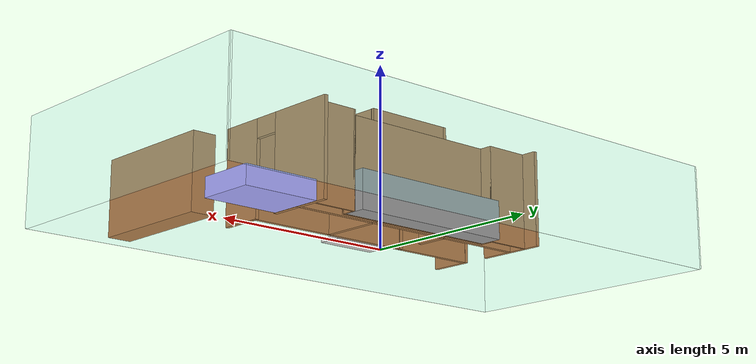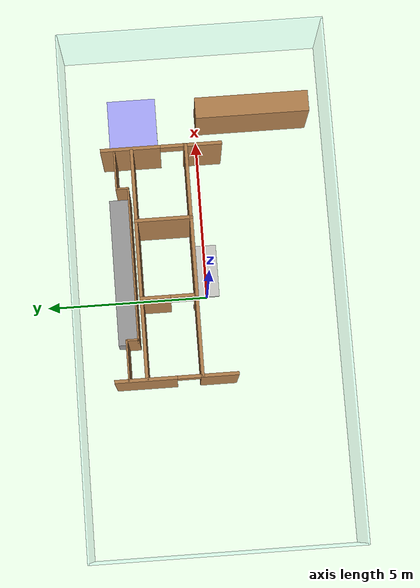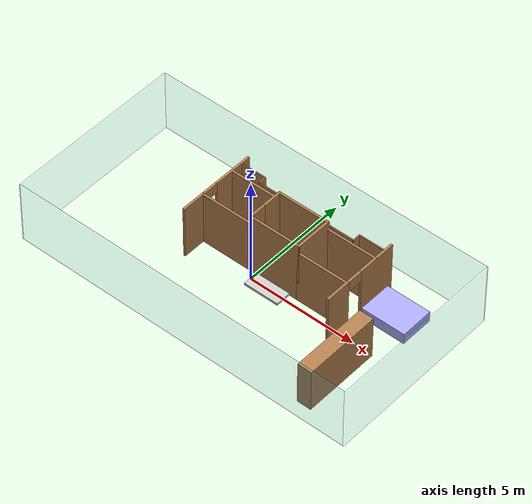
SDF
<?xml version='1.0'?>
<sdf version='1.6'>
  <model name='Farnsworth_House'>
    <link name='Wall_0'>
      <pose frame=''>0 4.05 0 0 -0 0</pose>
      <self_collide>0</self_collide>
      <kinematic>0</kinematic>
      <gravity>1</gravity>
      <inertial>
        <mass>1</mass>
        <pose frame=''>0 0 0 0 -0 0</pose>
        <inertia>
          <ixx>1</ixx>
          <ixy>0</ixy>
          <ixz>0</ixz>
          <iyy>1</iyy>
          <iyz>0</iyz>
          <izz>1</izz>
        </inertia>
      </inertial>
      <visual name='Wall_0_Visual'>
        <pose frame=''>0 0 1.435 0 -0 0</pose>
        <geometry>
          <box>
            <size>15.9002 0.05 2.87</size>
          </box>
        </geometry>
        <material>
          <script>
            <uri>file://media/materials/scripts/gazebo.material</uri>
            <name>Gazebo/Grey</name>
          </script>
          <ambient>0.6 1 1 1</ambient>
          <shader type='pixel'>
            <normal_map>__default__</normal_map>
          </shader>
          <diffuse>0.7 0.7 0.7 1</diffuse>
          <specular>0.01 0.01 0.01 1</specular>
          <emissive>0 0 0 1</emissive>
        </material>
        <meta>
          <layer>0</layer>
        </meta>
        <transparency>0.85</transparency>
        <cast_shadows>1</cast_shadows>
      </visual>
      <collision name='Wall_0_Collision'>
        <laser_retro>0</laser_retro>
        <max_contacts>10</max_contacts>
        <pose frame=''>0 0 1.435 0 -0 0</pose>
        <geometry>
          <box>
            <size>15.9002 0.05 2.87</size>
          </box>
        </geometry>
        <surface>
          <friction>
            <ode>
              <mu>1</mu>
              <mu2>1</mu2>
              <fdir1>0 0 0</fdir1>
              <slip1>0</slip1>
              <slip2>0</slip2>
            </ode>
            <torsional>
              <coefficient>1</coefficient>
              <patch_radius>0</patch_radius>
              <surface_radius>0</surface_radius>
              <use_patch_radius>1</use_patch_radius>
              <ode>
                <slip>0</slip>
              </ode>
            </torsional>
          </friction>
          <bounce>
            <restitution_coefficient>0</restitution_coefficient>
            <threshold>1e+06</threshold>
          </bounce>
          <contact>
            <collide_without_contact>0</collide_without_contact>
            <collide_without_contact_bitmask>1</collide_without_contact_bitmask>
            <collide_bitmask>1</collide_bitmask>
            <ode>
              <soft_cfm>0</soft_cfm>
              <soft_erp>0.2</soft_erp>
              <kp>1e+13</kp>
              <kd>1</kd>
              <max_vel>0.01</max_vel>
              <min_depth>0</min_depth>
            </ode>
            <bullet>
              <split_impulse>1</split_impulse>
              <split_impulse_penetration_threshold>-0.01</split_impulse_penetration_threshold>
              <soft_cfm>0</soft_cfm>
              <soft_erp>0.2</soft_erp>
              <kp>1e+13</kp>
              <kd>1</kd>
            </bullet>
          </contact>
        </surface>
      </collision>
    </link>
    <link name='Wall_1'>
      <pose frame=''>7.925 0 0 0 0 -1.5708</pose>
      <self_collide>0</self_collide>
      <kinematic>0</kinematic>
      <gravity>1</gravity>
      <inertial>
        <mass>1</mass>
        <pose frame=''>0 0 0 0 -0 0</pose>
        <inertia>
          <ixx>1</ixx>
          <ixy>0</ixy>
          <ixz>0</ixz>
          <iyy>1</iyy>
          <iyz>0</iyz>
          <izz>1</izz>
        </inertia>
      </inertial>
      <visual name='Wall_1_Visual'>
        <pose frame=''>0 0 1.435 0 -0 0</pose>
        <geometry>
          <box>
            <size>8.15019 0.05 2.87</size>
          </box>
        </geometry>
        <material>
          <script>
            <uri>file://media/materials/scripts/gazebo.material</uri>
            <name>Gazebo/Grey</name>
          </script>
          <ambient>0.6 1 1 1</ambient>
          <shader type='pixel'>
            <normal_map>__default__</normal_map>
          </shader>
          <diffuse>0.7 0.7 0.7 1</diffuse>
          <specular>0.01 0.01 0.01 1</specular>
          <emissive>0 0 0 1</emissive>
        </material>
        <meta>
          <layer>0</layer>
        </meta>
        <transparency>0.85</transparency>
        <cast_shadows>1</cast_shadows>
      </visual>
      <collision name='Wall_1_Collision'>
        <laser_retro>0</laser_retro>
        <max_contacts>10</max_contacts>
        <pose frame=''>0 0 1.435 0 -0 0</pose>
        <geometry>
          <box>
            <size>8.15019 0.05 2.87</size>
          </box>
        </geometry>
        <surface>
          <friction>
            <ode>
              <mu>1</mu>
              <mu2>1</mu2>
              <fdir1>0 0 0</fdir1>
              <slip1>0</slip1>
              <slip2>0</slip2>
            </ode>
            <torsional>
              <coefficient>1</coefficient>
              <patch_radius>0</patch_radius>
              <surface_radius>0</surface_radius>
              <use_patch_radius>1</use_patch_radius>
              <ode>
                <slip>0</slip>
              </ode>
            </torsional>
          </friction>
          <bounce>
            <restitution_coefficient>0</restitution_coefficient>
            <threshold>1e+06</threshold>
          </bounce>
          <contact>
            <collide_without_contact>0</collide_without_contact>
            <collide_without_contact_bitmask>1</collide_without_contact_bitmask>
            <collide_bitmask>1</collide_bitmask>
            <ode>
              <soft_cfm>0</soft_cfm>
              <soft_erp>0.2</soft_erp>
              <kp>1e+13</kp>
              <kd>1</kd>
              <max_vel>0.01</max_vel>
              <min_depth>0</min_depth>
            </ode>
            <bullet>
              <split_impulse>1</split_impulse>
              <split_impulse_penetration_threshold>-0.01</split_impulse_penetration_threshold>
              <soft_cfm>0</soft_cfm>
              <soft_erp>0.2</soft_erp>
              <kp>1e+13</kp>
              <kd>1</kd>
            </bullet>
          </contact>
        </surface>
      </collision>
    </link>
    <link name='Wall_10'>
      <pose frame=''>0.851 0.36 0 0 -0 0</pose>
      <self_collide>0</self_collide>
      <kinematic>0</kinematic>
      <visual name='Wall_10_Visual'>
        <pose frame=''>0 0 1.435 0 -0 0</pose>
        <geometry>
          <box>
            <size>2.45 0.1 2.87</size>
          </box>
        </geometry>
        <material>
          <script>
            <uri>file://media/materials/scripts/gazebo.material</uri>
            <name>Gazebo/Wood</name>
          </script>
          <ambient>1 1 1 1</ambient>
          <shader type='pixel'/>
          <diffuse>1 1 1 1</diffuse>
          <specular>0.2 0.2 0.2 1</specular>
          <emissive>0 0 0 1</emissive>
        </material>
        <meta>
          <layer>0</layer>
        </meta>
        <transparency>0</transparency>
        <cast_shadows>1</cast_shadows>
      </visual>
      <collision name='Wall_10_Collision'>
        <laser_retro>0</laser_retro>
        <max_contacts>10</max_contacts>
        <pose frame=''>0 0 1.435 0 -0 0</pose>
        <geometry>
          <box>
            <size>2.45 0.1 2.87</size>
          </box>
        </geometry>
        <surface>
          <friction>
            <ode>
              <mu>1</mu>
              <mu2>1</mu2>
              <fdir1>0 0 0</fdir1>
              <slip1>0</slip1>
              <slip2>0</slip2>
            </ode>
            <torsional>
              <coefficient>1</coefficient>
              <patch_radius>0</patch_radius>
              <surface_radius>0</surface_radius>
              <use_patch_radius>1</use_patch_radius>
              <ode>
                <slip>0</slip>
              </ode>
            </torsional>
          </friction>
          <bounce>
            <restitution_coefficient>0</restitution_coefficient>
            <threshold>1e+06</threshold>
          </bounce>
          <contact>
            <collide_without_contact>0</collide_without_contact>
            <collide_without_contact_bitmask>1</collide_without_contact_bitmask>
            <collide_bitmask>1</collide_bitmask>
            <ode>
              <soft_cfm>0</soft_cfm>
              <soft_erp>0.2</soft_erp>
              <kp>1e+13</kp>
              <kd>1</kd>
              <max_vel>0.01</max_vel>
              <min_depth>0</min_depth>
            </ode>
            <bullet>
              <split_impulse>1</split_impulse>
              <split_impulse_penetration_threshold>-0.01</split_impulse_penetration_threshold>
              <soft_cfm>0</soft_cfm>
              <soft_erp>0.2</soft_erp>
              <kp>1e+13</kp>
              <kd>1</kd>
            </bullet>
          </contact>
        </surface>
      </collision>
    </link>
    <link name='Wall_11'>
      <pose frame=''>3.179 0.36 0 0 -0 0</pose>
      <self_collide>0</self_collide>
      <kinematic>0</kinematic>
      <visual name='Wall_11_Visual'>
        <pose frame=''>0 0 1.25 0 -0 0</pose>
        <geometry>
          <box>
            <size>2.406 0.1 2.5</size>
          </box>
        </geometry>
        <material>
          <script>
            <uri>file://media/materials/scripts/gazebo.material</uri>
            <name>Gazebo/Wood</name>
          </script>
          <ambient>1 1 1 1</ambient>
          <shader type='pixel'/>
          <diffuse>1 1 1 1</diffuse>
          <specular>0.2 0.2 0.2 1</specular>
          <emissive>0 0 0 1</emissive>
        </material>
        <meta>
          <layer>0</layer>
        </meta>
        <transparency>0</transparency>
        <cast_shadows>1</cast_shadows>
      </visual>
      <collision name='Wall_11_Collision'>
        <laser_retro>0</laser_retro>
        <max_contacts>10</max_contacts>
        <pose frame=''>0 0 1.25 0 -0 0</pose>
        <geometry>
          <box>
            <size>2.406 0.1 2.5</size>
          </box>
        </geometry>
        <surface>
          <friction>
            <ode>
              <mu>1</mu>
              <mu2>1</mu2>
              <fdir1>0 0 0</fdir1>
              <slip1>0</slip1>
              <slip2>0</slip2>
            </ode>
            <torsional>
              <coefficient>1</coefficient>
              <patch_radius>0</patch_radius>
              <surface_radius>0</surface_radius>
              <use_patch_radius>1</use_patch_radius>
              <ode>
                <slip>0</slip>
              </ode>
            </torsional>
          </friction>
          <bounce>
            <restitution_coefficient>0</restitution_coefficient>
            <threshold>1e+06</threshold>
          </bounce>
          <contact>
            <collide_without_contact>0</collide_without_contact>
            <collide_without_contact_bitmask>1</collide_without_contact_bitmask>
            <collide_bitmask>1</collide_bitmask>
            <ode>
              <soft_cfm>0</soft_cfm>
              <soft_erp>0.2</soft_erp>
              <kp>1e+13</kp>
              <kd>1</kd>
              <max_vel>0.01</max_vel>
              <min_depth>0</min_depth>
            </ode>
            <bullet>
              <split_impulse>1</split_impulse>
              <split_impulse_penetration_threshold>-0.01</split_impulse_penetration_threshold>
              <soft_cfm>0</soft_cfm>
              <soft_erp>0.2</soft_erp>
              <kp>1e+13</kp>
              <kd>1</kd>
            </bullet>
          </contact>
        </surface>
      </collision>
    </link>
    <link name='Wall_13'>
      <pose frame=''>0.851 2.013 0 0 -0 0</pose>
      <self_collide>0</self_collide>
      <kinematic>0</kinematic>
      <visual name='Wall_13_Visual'>
        <pose frame=''>0 0 1.435 0 -0 0</pose>
        <geometry>
          <box>
            <size>2.45 0.1 2.87</size>
          </box>
        </geometry>
        <material>
          <script>
            <uri>file://media/materials/scripts/gazebo.material</uri>
            <name>Gazebo/Wood</name>
          </script>
          <ambient>1 1 1 1</ambient>
          <shader type='pixel'/>
          <diffuse>1 1 1 1</diffuse>
          <specular>0.2 0.2 0.2 1</specular>
          <emissive>0 0 0 1</emissive>
        </material>
        <meta>
          <layer>0</layer>
        </meta>
        <transparency>0</transparency>
        <cast_shadows>1</cast_shadows>
      </visual>
      <collision name='Wall_13_Collision'>
        <laser_retro>0</laser_retro>
        <max_contacts>10</max_contacts>
        <pose frame=''>0 0 1.435 0 -0 0</pose>
        <geometry>
          <box>
            <size>2.45 0.1 2.87</size>
          </box>
        </geometry>
        <surface>
          <friction>
            <ode>
              <mu>1</mu>
              <mu2>1</mu2>
              <fdir1>0 0 0</fdir1>
              <slip1>0</slip1>
              <slip2>0</slip2>
            </ode>
            <torsional>
              <coefficient>1</coefficient>
              <patch_radius>0</patch_radius>
              <surface_radius>0</surface_radius>
              <use_patch_radius>1</use_patch_radius>
              <ode>
                <slip>0</slip>
              </ode>
            </torsional>
          </friction>
          <bounce>
            <restitution_coefficient>0</restitution_coefficient>
            <threshold>1e+06</threshold>
          </bounce>
          <contact>
            <collide_without_contact>0</collide_without_contact>
            <collide_without_contact_bitmask>1</collide_without_contact_bitmask>
            <collide_bitmask>1</collide_bitmask>
            <ode>
              <soft_cfm>0</soft_cfm>
              <soft_erp>0.2</soft_erp>
              <kp>1e+13</kp>
              <kd>1</kd>
              <max_vel>0.01</max_vel>
              <min_depth>0</min_depth>
            </ode>
            <bullet>
              <split_impulse>1</split_impulse>
              <split_impulse_penetration_threshold>-0.01</split_impulse_penetration_threshold>
              <soft_cfm>0</soft_cfm>
              <soft_erp>0.2</soft_erp>
              <kp>1e+13</kp>
              <kd>1</kd>
            </bullet>
          </contact>
        </surface>
      </collision>
    </link>
    <link name='Wall_14'>
      <pose frame=''>2.026 1.1865 0 0 0 -1.5708</pose>
      <self_collide>0</self_collide>
      <kinematic>0</kinematic>
      <visual name='Wall_14_Visual'>
        <pose frame=''>0 0 1.435 0 -0 0</pose>
        <geometry>
          <box>
            <size>1.753 0.1 2.87</size>
          </box>
        </geometry>
        <material>
          <script>
            <uri>file://media/materials/scripts/gazebo.material</uri>
            <name>Gazebo/Wood</name>
          </script>
          <ambient>1 1 1 1</ambient>
          <shader type='pixel'/>
          <diffuse>1 1 1 1</diffuse>
          <specular>0.2 0.2 0.2 1</specular>
          <emissive>0 0 0 1</emissive>
        </material>
        <meta>
          <layer>0</layer>
        </meta>
        <transparency>0</transparency>
        <cast_shadows>1</cast_shadows>
      </visual>
      <collision name='Wall_14_Collision'>
        <laser_retro>0</laser_retro>
        <max_contacts>10</max_contacts>
        <pose frame=''>0 0 1.435 0 -0 0</pose>
        <geometry>
          <box>
            <size>1.753 0.1 2.87</size>
          </box>
        </geometry>
        <surface>
          <friction>
            <ode>
              <mu>1</mu>
              <mu2>1</mu2>
              <fdir1>0 0 0</fdir1>
              <slip1>0</slip1>
              <slip2>0</slip2>
            </ode>
            <torsional>
              <coefficient>1</coefficient>
              <patch_radius>0</patch_radius>
              <surface_radius>0</surface_radius>
              <use_patch_radius>1</use_patch_radius>
              <ode>
                <slip>0</slip>
              </ode>
            </torsional>
          </friction>
          <bounce>
            <restitution_coefficient>0</restitution_coefficient>
            <threshold>1e+06</threshold>
          </bounce>
          <contact>
            <collide_without_contact>0</collide_without_contact>
            <collide_without_contact_bitmask>1</collide_without_contact_bitmask>
            <collide_bitmask>1</collide_bitmask>
            <ode>
              <soft_cfm>0</soft_cfm>
              <soft_erp>0.2</soft_erp>
              <kp>1e+13</kp>
              <kd>1</kd>
              <max_vel>0.01</max_vel>
              <min_depth>0</min_depth>
            </ode>
            <bullet>
              <split_impulse>1</split_impulse>
              <split_impulse_penetration_threshold>-0.01</split_impulse_penetration_threshold>
              <soft_cfm>0</soft_cfm>
              <soft_erp>0.2</soft_erp>
              <kp>1e+13</kp>
              <kd>1</kd>
            </bullet>
          </contact>
        </surface>
      </collision>
    </link>
    <link name='Wall_16'>
      <pose frame=''>-0.324 1.1865 0 0 0 -1.5708</pose>
      <inertial>
        <mass>1</mass>
        <pose frame=''>0 0 0 0 -0 0</pose>
        <inertia>
          <ixx>1</ixx>
          <ixy>0</ixy>
          <ixz>0</ixz>
          <iyy>1</iyy>
          <iyz>0</iyz>
          <izz>1</izz>
        </inertia>
      </inertial>
      <self_collide>0</self_collide>
      <kinematic>0</kinematic>
      <visual name='Wall_16_Visual_0'>
        <pose frame=''>-0.414 0 1.435 0 -0 0</pose>
        <geometry>
          <box>
            <size>0.925 0.1 2.87</size>
          </box>
        </geometry>
        <material>
          <script>
            <uri>file://media/materials/scripts/gazebo.material</uri>
            <name>Gazebo/Wood</name>
          </script>
          <ambient>1 1 1 1</ambient>
          <shader type='pixel'>
            <normal_map>__default__</normal_map>
          </shader>
          <diffuse>1 1 1 1</diffuse>
          <specular>0.2 0.2 0.2 1</specular>
          <emissive>0 0 0 1</emissive>
        </material>
        <meta>
          <layer>0</layer>
        </meta>
        <transparency>0</transparency>
        <cast_shadows>1</cast_shadows>
      </visual>
      <visual name='Wall_16_Visual_1'>
        <pose frame=''>0.8125 0 1.435 0 -0 0</pose>
        <geometry>
          <box>
            <size>0.128 0.1 2.87</size>
          </box>
        </geometry>
        <material>
          <script>
            <uri>file://media/materials/scripts/gazebo.material</uri>
            <name>Gazebo/Wood</name>
          </script>
          <ambient>1 1 1 1</ambient>
          <shader type='pixel'>
            <normal_map>__default__</normal_map>
          </shader>
          <diffuse>1 1 1 1</diffuse>
          <specular>0.2 0.2 0.2 1</specular>
          <emissive>0 0 0 1</emissive>
        </material>
        <meta>
          <layer>0</layer>
        </meta>
        <transparency>0</transparency>
        <cast_shadows>1</cast_shadows>
      </visual>
      <visual name='Wall_16_Visual_3'>
        <pose frame=''>0.3985 0 2.435 0 -0 0</pose>
        <geometry>
          <box>
            <size>0.7 0.1 0.87</size>
          </box>
        </geometry>
        <material>
          <script>
            <uri>file://media/materials/scripts/gazebo.material</uri>
            <name>Gazebo/Wood</name>
          </script>
          <ambient>1 1 1 1</ambient>
          <shader type='pixel'>
            <normal_map>__default__</normal_map>
          </shader>
          <diffuse>1 1 1 1</diffuse>
          <specular>0.2 0.2 0.2 1</specular>
          <emissive>0 0 0 1</emissive>
        </material>
        <meta>
          <layer>0</layer>
        </meta>
        <transparency>0</transparency>
        <cast_shadows>1</cast_shadows>
      </visual>
      <collision name='Wall_16_Collision_0'>
        <laser_retro>0</laser_retro>
        <max_contacts>10</max_contacts>
        <pose frame=''>-0.414 0 1.435 0 -0 0</pose>
        <geometry>
          <box>
            <size>0.925 0.1 2.87</size>
          </box>
        </geometry>
        <surface>
          <friction>
            <ode>
              <mu>1</mu>
              <mu2>1</mu2>
              <fdir1>0 0 0</fdir1>
              <slip1>0</slip1>
              <slip2>0</slip2>
            </ode>
            <torsional>
              <coefficient>1</coefficient>
              <patch_radius>0</patch_radius>
              <surface_radius>0</surface_radius>
              <use_patch_radius>1</use_patch_radius>
              <ode>
                <slip>0</slip>
              </ode>
            </torsional>
          </friction>
          <bounce>
            <restitution_coefficient>0</restitution_coefficient>
            <threshold>1e+06</threshold>
          </bounce>
          <contact>
            <collide_without_contact>0</collide_without_contact>
            <collide_without_contact_bitmask>1</collide_without_contact_bitmask>
            <collide_bitmask>1</collide_bitmask>
            <ode>
              <soft_cfm>0</soft_cfm>
              <soft_erp>0.2</soft_erp>
              <kp>1e+13</kp>
              <kd>1</kd>
              <max_vel>0.01</max_vel>
              <min_depth>0</min_depth>
            </ode>
            <bullet>
              <split_impulse>1</split_impulse>
              <split_impulse_penetration_threshold>-0.01</split_impulse_penetration_threshold>
              <soft_cfm>0</soft_cfm>
              <soft_erp>0.2</soft_erp>
              <kp>1e+13</kp>
              <kd>1</kd>
            </bullet>
          </contact>
        </surface>
      </collision>
      <collision name='Wall_16_Collision_1'>
        <laser_retro>0</laser_retro>
        <max_contacts>10</max_contacts>
        <pose frame=''>0.8125 0 1.435 0 -0 0</pose>
        <geometry>
          <box>
            <size>0.128 0.1 2.87</size>
          </box>
        </geometry>
        <surface>
          <friction>
            <ode>
              <mu>1</mu>
              <mu2>1</mu2>
              <fdir1>0 0 0</fdir1>
              <slip1>0</slip1>
              <slip2>0</slip2>
            </ode>
            <torsional>
              <coefficient>1</coefficient>
              <patch_radius>0</patch_radius>
              <surface_radius>0</surface_radius>
              <use_patch_radius>1</use_patch_radius>
              <ode>
                <slip>0</slip>
              </ode>
            </torsional>
          </friction>
          <bounce>
            <restitution_coefficient>0</restitution_coefficient>
            <threshold>1e+06</threshold>
          </bounce>
          <contact>
            <collide_without_contact>0</collide_without_contact>
            <collide_without_contact_bitmask>1</collide_without_contact_bitmask>
            <collide_bitmask>1</collide_bitmask>
            <ode>
              <soft_cfm>0</soft_cfm>
              <soft_erp>0.2</soft_erp>
              <kp>1e+13</kp>
              <kd>1</kd>
              <max_vel>0.01</max_vel>
              <min_depth>0</min_depth>
            </ode>
            <bullet>
              <split_impulse>1</split_impulse>
              <split_impulse_penetration_threshold>-0.01</split_impulse_penetration_threshold>
              <soft_cfm>0</soft_cfm>
              <soft_erp>0.2</soft_erp>
              <kp>1e+13</kp>
              <kd>1</kd>
            </bullet>
          </contact>
        </surface>
      </collision>
      <collision name='Wall_16_Collision_3'>
        <laser_retro>0</laser_retro>
        <max_contacts>10</max_contacts>
        <pose frame=''>0.3985 0 2.435 0 -0 0</pose>
        <geometry>
          <box>
            <size>0.7 0.1 0.87</size>
          </box>
        </geometry>
        <surface>
          <friction>
            <ode>
              <mu>1</mu>
              <mu2>1</mu2>
              <fdir1>0 0 0</fdir1>
              <slip1>0</slip1>
              <slip2>0</slip2>
            </ode>
            <torsional>
              <coefficient>1</coefficient>
              <patch_radius>0</patch_radius>
              <surface_radius>0</surface_radius>
              <use_patch_radius>1</use_patch_radius>
              <ode>
                <slip>0</slip>
              </ode>
            </torsional>
          </friction>
          <bounce>
            <restitution_coefficient>0</restitution_coefficient>
            <threshold>1e+06</threshold>
          </bounce>
          <contact>
            <collide_without_contact>0</collide_without_contact>
            <collide_without_contact_bitmask>1</collide_without_contact_bitmask>
            <collide_bitmask>1</collide_bitmask>
            <ode>
              <soft_cfm>0</soft_cfm>
              <soft_erp>0.2</soft_erp>
              <kp>1e+13</kp>
              <kd>1</kd>
              <max_vel>0.01</max_vel>
              <min_depth>0</min_depth>
            </ode>
            <bullet>
              <split_impulse>1</split_impulse>
              <split_impulse_penetration_threshold>-0.01</split_impulse_penetration_threshold>
              <soft_cfm>0</soft_cfm>
              <soft_erp>0.2</soft_erp>
              <kp>1e+13</kp>
              <kd>1</kd>
            </bullet>
          </contact>
        </surface>
      </collision>
    </link>
    <link name='Wall_18'>
      <pose frame=''>-1.499 2.013 0 0 -0 3.14159</pose>
      <self_collide>0</self_collide>
      <kinematic>0</kinematic>
      <visual name='Wall_18_Visual'>
        <pose frame=''>0 0 1.25 0 -0 0</pose>
        <geometry>
          <box>
            <size>2.45 0.1 2.5</size>
          </box>
        </geometry>
        <material>
          <script>
            <uri>file://media/materials/scripts/gazebo.material</uri>
            <name>Gazebo/Wood</name>
          </script>
          <ambient>1 1 1 1</ambient>
          <shader type='pixel'/>
          <diffuse>1 1 1 1</diffuse>
          <specular>0.2 0.2 0.2 1</specular>
          <emissive>0 0 0 1</emissive>
        </material>
        <meta>
          <layer>0</layer>
        </meta>
        <transparency>0</transparency>
        <cast_shadows>1</cast_shadows>
      </visual>
      <collision name='Wall_18_Collision'>
        <laser_retro>0</laser_retro>
        <max_contacts>10</max_contacts>
        <pose frame=''>0 0 1.25 0 -0 0</pose>
        <geometry>
          <box>
            <size>2.45 0.1 2.5</size>
          </box>
        </geometry>
        <surface>
          <friction>
            <ode>
              <mu>1</mu>
              <mu2>1</mu2>
              <fdir1>0 0 0</fdir1>
              <slip1>0</slip1>
              <slip2>0</slip2>
            </ode>
            <torsional>
              <coefficient>1</coefficient>
              <patch_radius>0</patch_radius>
              <surface_radius>0</surface_radius>
              <use_patch_radius>1</use_patch_radius>
              <ode>
                <slip>0</slip>
              </ode>
            </torsional>
          </friction>
          <bounce>
            <restitution_coefficient>0</restitution_coefficient>
            <threshold>1e+06</threshold>
          </bounce>
          <contact>
            <collide_without_contact>0</collide_without_contact>
            <collide_without_contact_bitmask>1</collide_without_contact_bitmask>
            <collide_bitmask>1</collide_bitmask>
            <ode>
              <soft_cfm>0</soft_cfm>
              <soft_erp>0.2</soft_erp>
              <kp>1e+13</kp>
              <kd>1</kd>
              <max_vel>0.01</max_vel>
              <min_depth>0</min_depth>
            </ode>
            <bullet>
              <split_impulse>1</split_impulse>
              <split_impulse_penetration_threshold>-0.01</split_impulse_penetration_threshold>
              <soft_cfm>0</soft_cfm>
              <soft_erp>0.2</soft_erp>
              <kp>1e+13</kp>
              <kd>1</kd>
            </bullet>
          </contact>
        </surface>
      </collision>
    </link>
    <link name='Wall_2'>
      <pose frame=''>0 -4.05 0 0 -0 3.14159</pose>
      <self_collide>0</self_collide>
      <kinematic>0</kinematic>
      <gravity>1</gravity>
      <inertial>
        <mass>1</mass>
        <pose frame=''>0 0 0 0 -0 0</pose>
        <inertia>
          <ixx>1</ixx>
          <ixy>0</ixy>
          <ixz>0</ixz>
          <iyy>1</iyy>
          <iyz>0</iyz>
          <izz>1</izz>
        </inertia>
      </inertial>
      <visual name='Wall_2_Visual'>
        <pose frame=''>0 0 1.435 0 -0 0</pose>
        <geometry>
          <box>
            <size>15.8998 0.05 2.87</size>
          </box>
        </geometry>
        <material>
          <script>
            <uri>file://media/materials/scripts/gazebo.material</uri>
            <name>Gazebo/Grey</name>
          </script>
          <ambient>0.6 1 1 1</ambient>
          <shader type='pixel'>
            <normal_map>__default__</normal_map>
          </shader>
          <diffuse>0.7 0.7 0.7 1</diffuse>
          <specular>0.01 0.01 0.01 1</specular>
          <emissive>0 0 0 1</emissive>
        </material>
        <meta>
          <layer>0</layer>
        </meta>
        <transparency>0.85</transparency>
        <cast_shadows>1</cast_shadows>
      </visual>
      <collision name='Wall_2_Collision'>
        <laser_retro>0</laser_retro>
        <max_contacts>10</max_contacts>
        <pose frame=''>0 0 1.435 0 -0 0</pose>
        <geometry>
          <box>
            <size>15.8998 0.05 2.87</size>
          </box>
        </geometry>
        <surface>
          <friction>
            <ode>
              <mu>1</mu>
              <mu2>1</mu2>
              <fdir1>0 0 0</fdir1>
              <slip1>0</slip1>
              <slip2>0</slip2>
            </ode>
            <torsional>
              <coefficient>1</coefficient>
              <patch_radius>0</patch_radius>
              <surface_radius>0</surface_radius>
              <use_patch_radius>1</use_patch_radius>
              <ode>
                <slip>0</slip>
              </ode>
            </torsional>
          </friction>
          <bounce>
            <restitution_coefficient>0</restitution_coefficient>
            <threshold>1e+06</threshold>
          </bounce>
          <contact>
            <collide_without_contact>0</collide_without_contact>
            <collide_without_contact_bitmask>1</collide_without_contact_bitmask>
            <collide_bitmask>1</collide_bitmask>
            <ode>
              <soft_cfm>0</soft_cfm>
              <soft_erp>0.2</soft_erp>
              <kp>1e+13</kp>
              <kd>1</kd>
              <max_vel>0.01</max_vel>
              <min_depth>0</min_depth>
            </ode>
            <bullet>
              <split_impulse>1</split_impulse>
              <split_impulse_penetration_threshold>-0.01</split_impulse_penetration_threshold>
              <soft_cfm>0</soft_cfm>
              <soft_erp>0.2</soft_erp>
              <kp>1e+13</kp>
              <kd>1</kd>
            </bullet>
          </contact>
        </surface>
      </collision>
    </link>
    <link name='Wall_20'>
      <pose frame=''>3.175 2.013 0 0 -0 0</pose>
      <self_collide>0</self_collide>
      <kinematic>0</kinematic>
      <visual name='Wall_20_Visual'>
        <pose frame=''>0 0 1.25 0 -0 0</pose>
        <geometry>
          <box>
            <size>2.398 0.1 2.5</size>
          </box>
        </geometry>
        <material>
          <script>
            <uri>file://media/materials/scripts/gazebo.material</uri>
            <name>Gazebo/Wood</name>
          </script>
          <ambient>1 1 1 1</ambient>
          <shader type='pixel'/>
          <diffuse>1 1 1 1</diffuse>
          <specular>0.2 0.2 0.2 1</specular>
          <emissive>0 0 0 1</emissive>
        </material>
        <meta>
          <layer>0</layer>
        </meta>
        <transparency>0</transparency>
        <cast_shadows>1</cast_shadows>
      </visual>
      <collision name='Wall_20_Collision'>
        <laser_retro>0</laser_retro>
        <max_contacts>10</max_contacts>
        <pose frame=''>0 0 1.25 0 -0 0</pose>
        <geometry>
          <box>
            <size>2.398 0.1 2.5</size>
          </box>
        </geometry>
        <surface>
          <friction>
            <ode>
              <mu>1</mu>
              <mu2>1</mu2>
              <fdir1>0 0 0</fdir1>
              <slip1>0</slip1>
              <slip2>0</slip2>
            </ode>
            <torsional>
              <coefficient>1</coefficient>
              <patch_radius>0</patch_radius>
              <surface_radius>0</surface_radius>
              <use_patch_radius>1</use_patch_radius>
              <ode>
                <slip>0</slip>
              </ode>
            </torsional>
          </friction>
          <bounce>
            <restitution_coefficient>0</restitution_coefficient>
            <threshold>1e+06</threshold>
          </bounce>
          <contact>
            <collide_without_contact>0</collide_without_contact>
            <collide_without_contact_bitmask>1</collide_without_contact_bitmask>
            <collide_bitmask>1</collide_bitmask>
            <ode>
              <soft_cfm>0</soft_cfm>
              <soft_erp>0.2</soft_erp>
              <kp>1e+13</kp>
              <kd>1</kd>
              <max_vel>0.01</max_vel>
              <min_depth>0</min_depth>
            </ode>
            <bullet>
              <split_impulse>1</split_impulse>
              <split_impulse_penetration_threshold>-0.01</split_impulse_penetration_threshold>
              <soft_cfm>0</soft_cfm>
              <soft_erp>0.2</soft_erp>
              <kp>1e+13</kp>
              <kd>1</kd>
            </bullet>
          </contact>
        </surface>
      </collision>
    </link>
    <link name='Wall_27'>
      <pose frame=''>-2.084 2.54 0 0 -0 0</pose>
      <self_collide>0</self_collide>
      <kinematic>0</kinematic>
      <visual name='Wall_27_Visual'>
        <pose frame=''>0 0 1.25 0 -0 0</pose>
        <geometry>
          <box>
            <size>1.25 0.05 2.5</size>
          </box>
        </geometry>
        <material>
          <script>
            <uri>file://media/materials/scripts/gazebo.material</uri>
            <name>Gazebo/Wood</name>
          </script>
          <ambient>1 1 1 1</ambient>
          <shader type='pixel'/>
          <diffuse>1 1 1 1</diffuse>
          <specular>0.2 0.2 0.2 1</specular>
          <emissive>0 0 0 1</emissive>
        </material>
        <meta>
          <layer>0</layer>
        </meta>
        <transparency>0</transparency>
        <cast_shadows>1</cast_shadows>
      </visual>
      <collision name='Wall_27_Collision'>
        <laser_retro>0</laser_retro>
        <max_contacts>10</max_contacts>
        <pose frame=''>0 0 1.25 0 -0 0</pose>
        <geometry>
          <box>
            <size>1.25 0.05 2.5</size>
          </box>
        </geometry>
        <surface>
          <friction>
            <ode>
              <mu>1</mu>
              <mu2>1</mu2>
              <fdir1>0 0 0</fdir1>
              <slip1>0</slip1>
              <slip2>0</slip2>
            </ode>
            <torsional>
              <coefficient>1</coefficient>
              <patch_radius>0</patch_radius>
              <surface_radius>0</surface_radius>
              <use_patch_radius>1</use_patch_radius>
              <ode>
                <slip>0</slip>
              </ode>
            </torsional>
          </friction>
          <bounce>
            <restitution_coefficient>0</restitution_coefficient>
            <threshold>1e+06</threshold>
          </bounce>
          <contact>
            <collide_without_contact>0</collide_without_contact>
            <collide_without_contact_bitmask>1</collide_without_contact_bitmask>
            <collide_bitmask>1</collide_bitmask>
            <ode>
              <soft_cfm>0</soft_cfm>
              <soft_erp>0.2</soft_erp>
              <kp>1e+13</kp>
              <kd>1</kd>
              <max_vel>0.01</max_vel>
              <min_depth>0</min_depth>
            </ode>
            <bullet>
              <split_impulse>1</split_impulse>
              <split_impulse_penetration_threshold>-0.01</split_impulse_penetration_threshold>
              <soft_cfm>0</soft_cfm>
              <soft_erp>0.2</soft_erp>
              <kp>1e+13</kp>
              <kd>1</kd>
            </bullet>
          </contact>
        </surface>
      </collision>
    </link>
    <link name='Wall_29'>
      <pose frame=''>3.724 2.54 0 0 -0 0</pose>
      <self_collide>0</self_collide>
      <kinematic>0</kinematic>
      <visual name='Wall_29_Visual'>
        <pose frame=''>0 0 1.25 0 -0 0</pose>
        <geometry>
          <box>
            <size>1.25 0.05 2.5</size>
          </box>
        </geometry>
        <material>
          <script>
            <uri>file://media/materials/scripts/gazebo.material</uri>
            <name>Gazebo/Wood</name>
          </script>
          <ambient>1 1 1 1</ambient>
          <shader type='pixel'/>
          <diffuse>1 1 1 1</diffuse>
          <specular>0.2 0.2 0.2 1</specular>
          <emissive>0 0 0 1</emissive>
        </material>
        <meta>
          <layer>0</layer>
        </meta>
        <transparency>0</transparency>
        <cast_shadows>1</cast_shadows>
      </visual>
      <collision name='Wall_29_Collision'>
        <laser_retro>0</laser_retro>
        <max_contacts>10</max_contacts>
        <pose frame=''>0 0 1.25 0 -0 0</pose>
        <geometry>
          <box>
            <size>1.25 0.05 2.5</size>
          </box>
        </geometry>
        <surface>
          <friction>
            <ode>
              <mu>1</mu>
              <mu2>1</mu2>
              <fdir1>0 0 0</fdir1>
              <slip1>0</slip1>
              <slip2>0</slip2>
            </ode>
            <torsional>
              <coefficient>1</coefficient>
              <patch_radius>0</patch_radius>
              <surface_radius>0</surface_radius>
              <use_patch_radius>1</use_patch_radius>
              <ode>
                <slip>0</slip>
              </ode>
            </torsional>
          </friction>
          <bounce>
            <restitution_coefficient>0</restitution_coefficient>
            <threshold>1e+06</threshold>
          </bounce>
          <contact>
            <collide_without_contact>0</collide_without_contact>
            <collide_without_contact_bitmask>1</collide_without_contact_bitmask>
            <collide_bitmask>1</collide_bitmask>
            <ode>
              <soft_cfm>0</soft_cfm>
              <soft_erp>0.2</soft_erp>
              <kp>1e+13</kp>
              <kd>1</kd>
              <max_vel>0.01</max_vel>
              <min_depth>0</min_depth>
            </ode>
            <bullet>
              <split_impulse>1</split_impulse>
              <split_impulse_penetration_threshold>-0.01</split_impulse_penetration_threshold>
              <soft_cfm>0</soft_cfm>
              <soft_erp>0.2</soft_erp>
              <kp>1e+13</kp>
              <kd>1</kd>
            </bullet>
          </contact>
        </surface>
      </collision>
    </link>
    <link name='Wall_3'>
      <pose frame=''>-7.925 0 0 0 -0 1.5708</pose>
      <self_collide>0</self_collide>
      <kinematic>0</kinematic>
      <gravity>1</gravity>
      <inertial>
        <mass>1</mass>
        <pose frame=''>0 0 0 0 -0 0</pose>
        <inertia>
          <ixx>1</ixx>
          <ixy>0</ixy>
          <ixz>0</ixz>
          <iyy>1</iyy>
          <iyz>0</iyz>
          <izz>1</izz>
        </inertia>
      </inertial>
      <visual name='Wall_3_Visual_0'>
        <pose frame=''>0 0 1.435 0 -0 0</pose>
        <geometry>
          <box>
            <size>8.15019 0.05 2.87</size>
          </box>
        </geometry>
        <material>
          <script>
            <uri>file://media/materials/scripts/gazebo.material</uri>
            <name>Gazebo/Grey</name>
          </script>
          <ambient>0.6 1 1 1</ambient>
          <shader type='pixel'>
            <normal_map>__default__</normal_map>
          </shader>
          <diffuse>0.7 0.7 0.7 1</diffuse>
          <specular>0.01 0.01 0.01 1</specular>
          <emissive>0 0 0 1</emissive>
        </material>
        <meta>
          <layer>0</layer>
        </meta>
        <transparency>0.85</transparency>
        <cast_shadows>1</cast_shadows>
      </visual>
      <collision name='Wall_3_Collision_0'>
        <laser_retro>0</laser_retro>
        <max_contacts>10</max_contacts>
        <pose frame=''>0 0 1.435 0 -0 0</pose>
        <geometry>
          <box>
            <size>8.15019 0.05 2.87</size>
          </box>
        </geometry>
        <surface>
          <friction>
            <ode>
              <mu>1</mu>
              <mu2>1</mu2>
              <fdir1>0 0 0</fdir1>
              <slip1>0</slip1>
              <slip2>0</slip2>
            </ode>
            <torsional>
              <coefficient>1</coefficient>
              <patch_radius>0</patch_radius>
              <surface_radius>0</surface_radius>
              <use_patch_radius>1</use_patch_radius>
              <ode>
                <slip>0</slip>
              </ode>
            </torsional>
          </friction>
          <bounce>
            <restitution_coefficient>0</restitution_coefficient>
            <threshold>1e+06</threshold>
          </bounce>
          <contact>
            <collide_without_contact>0</collide_without_contact>
            <collide_without_contact_bitmask>1</collide_without_contact_bitmask>
            <collide_bitmask>1</collide_bitmask>
            <ode>
              <soft_cfm>0</soft_cfm>
              <soft_erp>0.2</soft_erp>
              <kp>1e+13</kp>
              <kd>1</kd>
              <max_vel>0.01</max_vel>
              <min_depth>0</min_depth>
            </ode>
            <bullet>
              <split_impulse>1</split_impulse>
              <split_impulse_penetration_threshold>-0.01</split_impulse_penetration_threshold>
              <soft_cfm>0</soft_cfm>
              <soft_erp>0.2</soft_erp>
              <kp>1e+13</kp>
              <kd>1</kd>
            </bullet>
          </contact>
        </surface>
      </collision>
    </link>
    <link name='Wall_31'>
      <pose frame=''>-1.484 2.365 0 0 0 -1.5708</pose>
      <self_collide>0</self_collide>
      <kinematic>0</kinematic>
      <visual name='Wall_31_Visual'>
        <pose frame=''>0 0 1.25 0 -0 0</pose>
        <geometry>
          <box>
            <size>0.4 0.05 2.5</size>
          </box>
        </geometry>
        <material>
          <script>
            <uri>file://media/materials/scripts/gazebo.material</uri>
            <name>Gazebo/Wood</name>
          </script>
          <ambient>1 1 1 1</ambient>
          <shader type='pixel'/>
          <diffuse>1 1 1 1</diffuse>
          <specular>0.2 0.2 0.2 1</specular>
          <emissive>0 0 0 1</emissive>
        </material>
        <meta>
          <layer>0</layer>
        </meta>
        <transparency>0</transparency>
        <cast_shadows>1</cast_shadows>
      </visual>
      <collision name='Wall_31_Collision'>
        <laser_retro>0</laser_retro>
        <max_contacts>10</max_contacts>
        <pose frame=''>0 0 1.25 0 -0 0</pose>
        <geometry>
          <box>
            <size>0.4 0.05 2.5</size>
          </box>
        </geometry>
        <surface>
          <friction>
            <ode>
              <mu>1</mu>
              <mu2>1</mu2>
              <fdir1>0 0 0</fdir1>
              <slip1>0</slip1>
              <slip2>0</slip2>
            </ode>
            <torsional>
              <coefficient>1</coefficient>
              <patch_radius>0</patch_radius>
              <surface_radius>0</surface_radius>
              <use_patch_radius>1</use_patch_radius>
              <ode>
                <slip>0</slip>
              </ode>
            </torsional>
          </friction>
          <bounce>
            <restitution_coefficient>0</restitution_coefficient>
            <threshold>1e+06</threshold>
          </bounce>
          <contact>
            <collide_without_contact>0</collide_without_contact>
            <collide_without_contact_bitmask>1</collide_without_contact_bitmask>
            <collide_bitmask>1</collide_bitmask>
            <ode>
              <soft_cfm>0</soft_cfm>
              <soft_erp>0.2</soft_erp>
              <kp>1e+13</kp>
              <kd>1</kd>
              <max_vel>0.01</max_vel>
              <min_depth>0</min_depth>
            </ode>
            <bullet>
              <split_impulse>1</split_impulse>
              <split_impulse_penetration_threshold>-0.01</split_impulse_penetration_threshold>
              <soft_cfm>0</soft_cfm>
              <soft_erp>0.2</soft_erp>
              <kp>1e+13</kp>
              <kd>1</kd>
            </bullet>
          </contact>
        </surface>
      </collision>
    </link>
    <link name='Wall_32'>
      <pose frame=''>0.82 2.19 0 0 -0 0</pose>
      <self_collide>0</self_collide>
      <kinematic>0</kinematic>
      <visual name='Wall_32_Visual'>
        <pose frame=''>0 0 1.25 0 -0 0</pose>
        <geometry>
          <box>
            <size>4.658 0.05 2.5</size>
          </box>
        </geometry>
        <material>
          <script>
            <uri>file://media/materials/scripts/gazebo.material</uri>
            <name>Gazebo/Wood</name>
          </script>
          <ambient>1 1 1 1</ambient>
          <shader type='pixel'/>
          <diffuse>1 1 1 1</diffuse>
          <specular>0.2 0.2 0.2 1</specular>
          <emissive>0 0 0 1</emissive>
        </material>
        <meta>
          <layer>0</layer>
        </meta>
        <transparency>0</transparency>
        <cast_shadows>1</cast_shadows>
      </visual>
      <collision name='Wall_32_Collision'>
        <laser_retro>0</laser_retro>
        <max_contacts>10</max_contacts>
        <pose frame=''>0 0 1.25 0 -0 0</pose>
        <geometry>
          <box>
            <size>4.658 0.05 2.5</size>
          </box>
        </geometry>
        <surface>
          <friction>
            <ode>
              <mu>1</mu>
              <mu2>1</mu2>
              <fdir1>0 0 0</fdir1>
              <slip1>0</slip1>
              <slip2>0</slip2>
            </ode>
            <torsional>
              <coefficient>1</coefficient>
              <patch_radius>0</patch_radius>
              <surface_radius>0</surface_radius>
              <use_patch_radius>1</use_patch_radius>
              <ode>
                <slip>0</slip>
              </ode>
            </torsional>
          </friction>
          <bounce>
            <restitution_coefficient>0</restitution_coefficient>
            <threshold>1e+06</threshold>
          </bounce>
          <contact>
            <collide_without_contact>0</collide_without_contact>
            <collide_without_contact_bitmask>1</collide_without_contact_bitmask>
            <collide_bitmask>1</collide_bitmask>
            <ode>
              <soft_cfm>0</soft_cfm>
              <soft_erp>0.2</soft_erp>
              <kp>1e+13</kp>
              <kd>1</kd>
              <max_vel>0.01</max_vel>
              <min_depth>0</min_depth>
            </ode>
            <bullet>
              <split_impulse>1</split_impulse>
              <split_impulse_penetration_threshold>-0.01</split_impulse_penetration_threshold>
              <soft_cfm>0</soft_cfm>
              <soft_erp>0.2</soft_erp>
              <kp>1e+13</kp>
              <kd>1</kd>
            </bullet>
          </contact>
        </surface>
      </collision>
    </link>
    <link name='Wall_33'>
      <pose frame=''>3.124 2.365 0 0 -0 1.5708</pose>
      <self_collide>0</self_collide>
      <kinematic>0</kinematic>
      <visual name='Wall_33_Visual'>
        <pose frame=''>0 0 1.25 0 -0 0</pose>
        <geometry>
          <box>
            <size>0.4 0.05 2.5</size>
          </box>
        </geometry>
        <material>
          <script>
            <uri>file://media/materials/scripts/gazebo.material</uri>
            <name>Gazebo/Wood</name>
          </script>
          <ambient>1 1 1 1</ambient>
          <shader type='pixel'/>
          <diffuse>1 1 1 1</diffuse>
          <specular>0.2 0.2 0.2 1</specular>
          <emissive>0 0 0 1</emissive>
        </material>
        <meta>
          <layer>0</layer>
        </meta>
        <transparency>0</transparency>
        <cast_shadows>1</cast_shadows>
      </visual>
      <collision name='Wall_33_Collision'>
        <laser_retro>0</laser_retro>
        <max_contacts>10</max_contacts>
        <pose frame=''>0 0 1.25 0 -0 0</pose>
        <geometry>
          <box>
            <size>0.4 0.05 2.5</size>
          </box>
        </geometry>
        <surface>
          <friction>
            <ode>
              <mu>1</mu>
              <mu2>1</mu2>
              <fdir1>0 0 0</fdir1>
              <slip1>0</slip1>
              <slip2>0</slip2>
            </ode>
            <torsional>
              <coefficient>1</coefficient>
              <patch_radius>0</patch_radius>
              <surface_radius>0</surface_radius>
              <use_patch_radius>1</use_patch_radius>
              <ode>
                <slip>0</slip>
              </ode>
            </torsional>
          </friction>
          <bounce>
            <restitution_coefficient>0</restitution_coefficient>
            <threshold>1e+06</threshold>
          </bounce>
          <contact>
            <collide_without_contact>0</collide_without_contact>
            <collide_without_contact_bitmask>1</collide_without_contact_bitmask>
            <collide_bitmask>1</collide_bitmask>
            <ode>
              <soft_cfm>0</soft_cfm>
              <soft_erp>0.2</soft_erp>
              <kp>1e+13</kp>
              <kd>1</kd>
              <max_vel>0.01</max_vel>
              <min_depth>0</min_depth>
            </ode>
            <bullet>
              <split_impulse>1</split_impulse>
              <split_impulse_penetration_threshold>-0.01</split_impulse_penetration_threshold>
              <soft_cfm>0</soft_cfm>
              <soft_erp>0.2</soft_erp>
              <kp>1e+13</kp>
              <kd>1</kd>
            </bullet>
          </contact>
        </surface>
      </collision>
    </link>
    <link name='Wall_37'>
      <pose frame=''>0.8245 2.534 0 0 -0 0</pose>
      <self_collide>0</self_collide>
      <kinematic>0</kinematic>
      <visual name='Wall_37_Visual'>
        <pose frame=''>0 0 0.5 0 -0 0</pose>
        <geometry>
          <box>
            <size>4.55152 0.6 1</size>
          </box>
        </geometry>
        <material>
          <script>
            <uri>file://media/materials/scripts/gazebo.material</uri>
            <name>Gazebo/Grey</name>
          </script>
          <ambient>1 1 1 1</ambient>
          <shader type='pixel'/>
          <diffuse>0.7 0.7 0.7 1</diffuse>
          <specular>0.01 0.01 0.01 1</specular>
          <emissive>0 0 0 1</emissive>
        </material>
        <meta>
          <layer>0</layer>
        </meta>
        <transparency>0</transparency>
        <cast_shadows>1</cast_shadows>
      </visual>
      <collision name='Wall_37_Collision'>
        <laser_retro>0</laser_retro>
        <max_contacts>10</max_contacts>
        <pose frame=''>0 0 0.5 0 -0 0</pose>
        <geometry>
          <box>
            <size>4.55152 0.6 1</size>
          </box>
        </geometry>
        <surface>
          <friction>
            <ode>
              <mu>1</mu>
              <mu2>1</mu2>
              <fdir1>0 0 0</fdir1>
              <slip1>0</slip1>
              <slip2>0</slip2>
            </ode>
            <torsional>
              <coefficient>1</coefficient>
              <patch_radius>0</patch_radius>
              <surface_radius>0</surface_radius>
              <use_patch_radius>1</use_patch_radius>
              <ode>
                <slip>0</slip>
              </ode>
            </torsional>
          </friction>
          <bounce>
            <restitution_coefficient>0</restitution_coefficient>
            <threshold>1e+06</threshold>
          </bounce>
          <contact>
            <collide_without_contact>0</collide_without_contact>
            <collide_without_contact_bitmask>1</collide_without_contact_bitmask>
            <collide_bitmask>1</collide_bitmask>
            <ode>
              <soft_cfm>0</soft_cfm>
              <soft_erp>0.2</soft_erp>
              <kp>1e+13</kp>
              <kd>1</kd>
              <max_vel>0.01</max_vel>
              <min_depth>0</min_depth>
            </ode>
            <bullet>
              <split_impulse>1</split_impulse>
              <split_impulse_penetration_threshold>-0.01</split_impulse_penetration_threshold>
              <soft_cfm>0</soft_cfm>
              <soft_erp>0.2</soft_erp>
              <kp>1e+13</kp>
              <kd>1</kd>
            </bullet>
          </contact>
        </surface>
      </collision>
    </link>
    <link name='Wall_39'>
      <pose frame=''>0.828 -0.04 0 0 -0 0</pose>
      <self_collide>0</self_collide>
      <kinematic>0</kinematic>
      <visual name='Wall_39_Visual'>
        <pose frame=''>0 0 0.05 0 -0 0</pose>
        <geometry>
          <box>
            <size>1.63986 0.7 0.1</size>
          </box>
        </geometry>
        <material>
          <script>
            <uri>file://media/materials/scripts/gazebo.material</uri>
            <name>Gazebo/CeilingTiled</name>
          </script>
          <ambient>1 1 1 1</ambient>
          <shader type='pixel'/>
          <diffuse>1 1 1 1</diffuse>
          <specular>0 0 0 1</specular>
          <emissive>0 0 0 1</emissive>
        </material>
        <meta>
          <layer>0</layer>
        </meta>
        <transparency>0</transparency>
        <cast_shadows>1</cast_shadows>
      </visual>
      <collision name='Wall_39_Collision'>
        <laser_retro>0</laser_retro>
        <max_contacts>10</max_contacts>
        <pose frame=''>0 0 0.05 0 -0 0</pose>
        <geometry>
          <box>
            <size>1.63986 0.7 0.1</size>
          </box>
        </geometry>
        <surface>
          <friction>
            <ode>
              <mu>1</mu>
              <mu2>1</mu2>
              <fdir1>0 0 0</fdir1>
              <slip1>0</slip1>
              <slip2>0</slip2>
            </ode>
            <torsional>
              <coefficient>1</coefficient>
              <patch_radius>0</patch_radius>
              <surface_radius>0</surface_radius>
              <use_patch_radius>1</use_patch_radius>
              <ode>
                <slip>0</slip>
              </ode>
            </torsional>
          </friction>
          <bounce>
            <restitution_coefficient>0</restitution_coefficient>
            <threshold>1e+06</threshold>
          </bounce>
          <contact>
            <collide_without_contact>0</collide_without_contact>
            <collide_without_contact_bitmask>1</collide_without_contact_bitmask>
            <collide_bitmask>1</collide_bitmask>
            <ode>
              <soft_cfm>0</soft_cfm>
              <soft_erp>0.2</soft_erp>
              <kp>1e+13</kp>
              <kd>1</kd>
              <max_vel>0.01</max_vel>
              <min_depth>0</min_depth>
            </ode>
            <bullet>
              <split_impulse>1</split_impulse>
              <split_impulse_penetration_threshold>-0.01</split_impulse_penetration_threshold>
              <soft_cfm>0</soft_cfm>
              <soft_erp>0.2</soft_erp>
              <kp>1e+13</kp>
              <kd>1</kd>
            </bullet>
          </contact>
        </surface>
      </collision>
    </link>
    <link name='Wall_41'>
      <pose frame=''>5.603 -1.768 0 0 0 -1.5708</pose>
      <self_collide>0</self_collide>
      <kinematic>0</kinematic>
      <visual name='Wall_41_Visual'>
        <pose frame=''>0 0 1 0 -0 0</pose>
        <geometry>
          <box>
            <size>3.5 0.65 2</size>
          </box>
        </geometry>
        <material>
          <script>
            <uri>file://media/materials/scripts/gazebo.material</uri>
            <name>Gazebo/Wood</name>
          </script>
          <ambient>1 1 1 1</ambient>
          <shader type='pixel'/>
          <diffuse>1 1 1 1</diffuse>
          <specular>0.2 0.2 0.2 1</specular>
          <emissive>0 0 0 1</emissive>
        </material>
        <meta>
          <layer>0</layer>
        </meta>
        <transparency>0</transparency>
        <cast_shadows>1</cast_shadows>
      </visual>
      <collision name='Wall_41_Collision'>
        <laser_retro>0</laser_retro>
        <max_contacts>10</max_contacts>
        <pose frame=''>0 0 1 0 -0 0</pose>
        <geometry>
          <box>
            <size>3.5 0.65 2</size>
          </box>
        </geometry>
        <surface>
          <friction>
            <ode>
              <mu>1</mu>
              <mu2>1</mu2>
              <fdir1>0 0 0</fdir1>
              <slip1>0</slip1>
              <slip2>0</slip2>
            </ode>
            <torsional>
              <coefficient>1</coefficient>
              <patch_radius>0</patch_radius>
              <surface_radius>0</surface_radius>
              <use_patch_radius>1</use_patch_radius>
              <ode>
                <slip>0</slip>
              </ode>
            </torsional>
          </friction>
          <bounce>
            <restitution_coefficient>0</restitution_coefficient>
            <threshold>1e+06</threshold>
          </bounce>
          <contact>
            <collide_without_contact>0</collide_without_contact>
            <collide_without_contact_bitmask>1</collide_without_contact_bitmask>
            <collide_bitmask>1</collide_bitmask>
            <ode>
              <soft_cfm>0</soft_cfm>
              <soft_erp>0.2</soft_erp>
              <kp>1e+13</kp>
              <kd>1</kd>
              <max_vel>0.01</max_vel>
              <min_depth>0</min_depth>
            </ode>
            <bullet>
              <split_impulse>1</split_impulse>
              <split_impulse_penetration_threshold>-0.01</split_impulse_penetration_threshold>
              <soft_cfm>0</soft_cfm>
              <soft_erp>0.2</soft_erp>
              <kp>1e+13</kp>
              <kd>1</kd>
            </bullet>
          </contact>
        </surface>
      </collision>
    </link>
    <link name='Wall_43'>
      <pose frame=''>5.41642 1.96377 0 0 -0 0</pose>
      <self_collide>0</self_collide>
      <kinematic>0</kinematic>
      <visual name='Wall_43_Visual'>
        <pose frame=''>0 0 0.25 0 -0 0</pose>
        <geometry>
          <box>
            <size>2.03 1.52 0.5</size>
          </box>
        </geometry>
        <material>
          <script>
            <uri>file://media/materials/scripts/gazebo.material</uri>
            <name>Gazebo/Grey</name>
          </script>
          <ambient>0.666667 0.666667 1 1</ambient>
          <shader type='pixel'/>
          <diffuse>0.7 0.7 0.7 1</diffuse>
          <specular>0.01 0.01 0.01 1</specular>
          <emissive>0 0 0 1</emissive>
        </material>
        <meta>
          <layer>0</layer>
        </meta>
        <transparency>0</transparency>
        <cast_shadows>1</cast_shadows>
      </visual>
      <collision name='Wall_43_Collision'>
        <laser_retro>0</laser_retro>
        <max_contacts>10</max_contacts>
        <pose frame=''>0 0 0.25 0 -0 0</pose>
        <geometry>
          <box>
            <size>2.03 1.52 0.5</size>
          </box>
        </geometry>
        <surface>
          <friction>
            <ode>
              <mu>1</mu>
              <mu2>1</mu2>
              <fdir1>0 0 0</fdir1>
              <slip1>0</slip1>
              <slip2>0</slip2>
            </ode>
            <torsional>
              <coefficient>1</coefficient>
              <patch_radius>0</patch_radius>
              <surface_radius>0</surface_radius>
              <use_patch_radius>1</use_patch_radius>
              <ode>
                <slip>0</slip>
              </ode>
            </torsional>
          </friction>
          <bounce>
            <restitution_coefficient>0</restitution_coefficient>
            <threshold>1e+06</threshold>
          </bounce>
          <contact>
            <collide_without_contact>0</collide_without_contact>
            <collide_without_contact_bitmask>1</collide_without_contact_bitmask>
            <collide_bitmask>1</collide_bitmask>
            <ode>
              <soft_cfm>0</soft_cfm>
              <soft_erp>0.2</soft_erp>
              <kp>1e+13</kp>
              <kd>1</kd>
              <max_vel>0.01</max_vel>
              <min_depth>0</min_depth>
            </ode>
            <bullet>
              <split_impulse>1</split_impulse>
              <split_impulse_penetration_threshold>-0.01</split_impulse_penetration_threshold>
              <soft_cfm>0</soft_cfm>
              <soft_erp>0.2</soft_erp>
              <kp>1e+13</kp>
              <kd>1</kd>
            </bullet>
          </contact>
        </surface>
      </collision>
    </link>
    <link name='Wall_5'>
      <pose frame=''>-2.694 1.128 0 0 0 -1.5708</pose>
      <inertial>
        <mass>1</mass>
        <pose frame=''>0 0 0 0 -0 0</pose>
        <inertia>
          <ixx>1</ixx>
          <ixy>0</ixy>
          <ixz>0</ixz>
          <iyy>1</iyy>
          <iyz>0</iyz>
          <izz>1</izz>
        </inertia>
      </inertial>
      <self_collide>0</self_collide>
      <kinematic>0</kinematic>
      <visual name='Wall_5_Visual_0'>
        <pose frame=''>-0.916961 0 1.25 0 -0 0</pose>
        <geometry>
          <box>
            <size>1.86591 0.1 2.5</size>
          </box>
        </geometry>
        <material>
          <script>
            <uri>file://media/materials/scripts/gazebo.material</uri>
            <name>Gazebo/Wood</name>
          </script>
          <ambient>1 1 1 1</ambient>
          <shader type='pixel'>
            <normal_map>__default__</normal_map>
          </shader>
          <diffuse>1 1 1 1</diffuse>
          <specular>0.2 0.2 0.2 1</specular>
          <emissive>0 0 0 1</emissive>
        </material>
        <meta>
          <layer>0</layer>
        </meta>
        <transparency>0</transparency>
        <cast_shadows>1</cast_shadows>
      </visual>
      <visual name='Wall_5_Visual_1'>
        <pose frame=''>1.28295 0 1.25 0 -0 0</pose>
        <geometry>
          <box>
            <size>1.13392 0.1 2.5</size>
          </box>
        </geometry>
        <material>
          <script>
            <uri>file://media/materials/scripts/gazebo.material</uri>
            <name>Gazebo/Wood</name>
          </script>
          <ambient>1 1 1 1</ambient>
          <shader type='pixel'>
            <normal_map>__default__</normal_map>
          </shader>
          <diffuse>1 1 1 1</diffuse>
          <specular>0.2 0.2 0.2 1</specular>
          <emissive>0 0 0 1</emissive>
        </material>
        <meta>
          <layer>0</layer>
        </meta>
        <transparency>0</transparency>
        <cast_shadows>1</cast_shadows>
      </visual>
      <visual name='Wall_5_Visual_2'>
        <pose frame=''>0.365993 0 2.25 0 -0 0</pose>
        <geometry>
          <box>
            <size>0.7 0.1 0.5</size>
          </box>
        </geometry>
        <material>
          <script>
            <uri>file://media/materials/scripts/gazebo.material</uri>
            <name>Gazebo/Wood</name>
          </script>
          <ambient>1 1 1 1</ambient>
          <shader type='pixel'>
            <normal_map>__default__</normal_map>
          </shader>
          <diffuse>1 1 1 1</diffuse>
          <specular>0.2 0.2 0.2 1</specular>
          <emissive>0 0 0 1</emissive>
        </material>
        <meta>
          <layer>0</layer>
        </meta>
        <transparency>0</transparency>
        <cast_shadows>1</cast_shadows>
      </visual>
      <collision name='Wall_5_Collision_0'>
        <laser_retro>0</laser_retro>
        <max_contacts>10</max_contacts>
        <pose frame=''>-0.916961 0 1.25 0 -0 0</pose>
        <geometry>
          <box>
            <size>1.86591 0.1 2.5</size>
          </box>
        </geometry>
        <surface>
          <friction>
            <ode>
              <mu>1</mu>
              <mu2>1</mu2>
              <fdir1>0 0 0</fdir1>
              <slip1>0</slip1>
              <slip2>0</slip2>
            </ode>
            <torsional>
              <coefficient>1</coefficient>
              <patch_radius>0</patch_radius>
              <surface_radius>0</surface_radius>
              <use_patch_radius>1</use_patch_radius>
              <ode>
                <slip>0</slip>
              </ode>
            </torsional>
          </friction>
          <bounce>
            <restitution_coefficient>0</restitution_coefficient>
            <threshold>1e+06</threshold>
          </bounce>
          <contact>
            <collide_without_contact>0</collide_without_contact>
            <collide_without_contact_bitmask>1</collide_without_contact_bitmask>
            <collide_bitmask>1</collide_bitmask>
            <ode>
              <soft_cfm>0</soft_cfm>
              <soft_erp>0.2</soft_erp>
              <kp>1e+13</kp>
              <kd>1</kd>
              <max_vel>0.01</max_vel>
              <min_depth>0</min_depth>
            </ode>
            <bullet>
              <split_impulse>1</split_impulse>
              <split_impulse_penetration_threshold>-0.01</split_impulse_penetration_threshold>
              <soft_cfm>0</soft_cfm>
              <soft_erp>0.2</soft_erp>
              <kp>1e+13</kp>
              <kd>1</kd>
            </bullet>
          </contact>
        </surface>
      </collision>
      <collision name='Wall_5_Collision_2'>
        <laser_retro>0</laser_retro>
        <max_contacts>10</max_contacts>
        <pose frame=''>0.365993 0 2.25 0 -0 0</pose>
        <geometry>
          <box>
            <size>0.7 0.1 0.5</size>
          </box>
        </geometry>
        <surface>
          <friction>
            <ode>
              <mu>1</mu>
              <mu2>1</mu2>
              <fdir1>0 0 0</fdir1>
              <slip1>0</slip1>
              <slip2>0</slip2>
            </ode>
            <torsional>
              <coefficient>1</coefficient>
              <patch_radius>0</patch_radius>
              <surface_radius>0</surface_radius>
              <use_patch_radius>1</use_patch_radius>
              <ode>
                <slip>0</slip>
              </ode>
            </torsional>
          </friction>
          <bounce>
            <restitution_coefficient>0</restitution_coefficient>
            <threshold>1e+06</threshold>
          </bounce>
          <contact>
            <collide_without_contact>0</collide_without_contact>
            <collide_without_contact_bitmask>1</collide_without_contact_bitmask>
            <collide_bitmask>1</collide_bitmask>
            <ode>
              <soft_cfm>0</soft_cfm>
              <soft_erp>0.2</soft_erp>
              <kp>1e+13</kp>
              <kd>1</kd>
              <max_vel>0.01</max_vel>
              <min_depth>0</min_depth>
            </ode>
            <bullet>
              <split_impulse>1</split_impulse>
              <split_impulse_penetration_threshold>-0.01</split_impulse_penetration_threshold>
              <soft_cfm>0</soft_cfm>
              <soft_erp>0.2</soft_erp>
              <kp>1e+13</kp>
              <kd>1</kd>
            </bullet>
          </contact>
        </surface>
      </collision>
      <collision name='Wall_5_Collision_1'>
        <laser_retro>0</laser_retro>
        <max_contacts>10</max_contacts>
        <pose frame=''>1.28295 0 1.25 0 -0 0</pose>
        <geometry>
          <box>
            <size>1.13392 0.1 2.5</size>
          </box>
        </geometry>
        <surface>
          <friction>
            <ode>
              <mu>1</mu>
              <mu2>1</mu2>
              <fdir1>0 0 0</fdir1>
              <slip1>0</slip1>
              <slip2>0</slip2>
            </ode>
            <torsional>
              <coefficient>1</coefficient>
              <patch_radius>0</patch_radius>
              <surface_radius>0</surface_radius>
              <use_patch_radius>1</use_patch_radius>
              <ode>
                <slip>0</slip>
              </ode>
            </torsional>
          </friction>
          <bounce>
            <restitution_coefficient>0</restitution_coefficient>
            <threshold>1e+06</threshold>
          </bounce>
          <contact>
            <collide_without_contact>0</collide_without_contact>
            <collide_without_contact_bitmask>1</collide_without_contact_bitmask>
            <collide_bitmask>1</collide_bitmask>
            <ode>
              <soft_cfm>0</soft_cfm>
              <soft_erp>0.2</soft_erp>
              <kp>1e+13</kp>
              <kd>1</kd>
              <max_vel>0.01</max_vel>
              <min_depth>0</min_depth>
            </ode>
            <bullet>
              <split_impulse>1</split_impulse>
              <split_impulse_penetration_threshold>-0.01</split_impulse_penetration_threshold>
              <soft_cfm>0</soft_cfm>
              <soft_erp>0.2</soft_erp>
              <kp>1e+13</kp>
              <kd>1</kd>
            </bullet>
          </contact>
        </surface>
      </collision>
    </link>
    <link name='Wall_7'>
      <pose frame=''>4.336 1.108 0 0 0 -1.5708</pose>
      <self_collide>0</self_collide>
      <kinematic>0</kinematic>
      <visual name='Wall_7_Visual_0'>
        <pose frame=''>-0.939957 0 1.25 0 -0 0</pose>
        <geometry>
          <box>
            <size>1.81991 0.1 2.5</size>
          </box>
        </geometry>
        <material>
          <script>
            <uri>file://media/materials/scripts/gazebo.material</uri>
            <name>Gazebo/Wood</name>
          </script>
          <ambient>1 1 1 1</ambient>
          <shader type='pixel'/>
          <diffuse>1 1 1 1</diffuse>
          <specular>0.2 0.2 0.2 1</specular>
          <emissive>0 0 0 1</emissive>
        </material>
        <meta>
          <layer>0</layer>
        </meta>
        <transparency>0</transparency>
        <cast_shadows>1</cast_shadows>
      </visual>
      <visual name='Wall_7_Visual_1'>
        <pose frame=''>1.25996 0 1.25 0 -0 0</pose>
        <geometry>
          <box>
            <size>1.17992 0.1 2.5</size>
          </box>
        </geometry>
        <material>
          <script>
            <uri>file://media/materials/scripts/gazebo.material</uri>
            <name>Gazebo/Wood</name>
          </script>
          <ambient>1 1 1 1</ambient>
          <shader type='pixel'/>
          <diffuse>1 1 1 1</diffuse>
          <specular>0.2 0.2 0.2 1</specular>
          <emissive>0 0 0 1</emissive>
        </material>
        <meta>
          <layer>0</layer>
        </meta>
        <transparency>0</transparency>
        <cast_shadows>1</cast_shadows>
      </visual>
      <visual name='Wall_7_Visual_2'>
        <pose frame=''>0.32 0 2.25 0 -0 0</pose>
        <geometry>
          <box>
            <size>0.7 0.1 0.5</size>
          </box>
        </geometry>
        <material>
          <script>
            <uri>file://media/materials/scripts/gazebo.material</uri>
            <name>Gazebo/Wood</name>
          </script>
          <ambient>1 1 1 1</ambient>
          <shader type='pixel'/>
          <diffuse>1 1 1 1</diffuse>
          <specular>0.2 0.2 0.2 1</specular>
          <emissive>0 0 0 1</emissive>
        </material>
        <meta>
          <layer>0</layer>
        </meta>
        <transparency>0</transparency>
        <cast_shadows>1</cast_shadows>
      </visual>
      <collision name='Wall_7_Collision_1'>
        <laser_retro>0</laser_retro>
        <max_contacts>10</max_contacts>
        <pose frame=''>1.25996 0 1.25 0 -0 0</pose>
        <geometry>
          <box>
            <size>1.17992 0.1 2.5</size>
          </box>
        </geometry>
        <surface>
          <friction>
            <ode>
              <mu>1</mu>
              <mu2>1</mu2>
              <fdir1>0 0 0</fdir1>
              <slip1>0</slip1>
              <slip2>0</slip2>
            </ode>
            <torsional>
              <coefficient>1</coefficient>
              <patch_radius>0</patch_radius>
              <surface_radius>0</surface_radius>
              <use_patch_radius>1</use_patch_radius>
              <ode>
                <slip>0</slip>
              </ode>
            </torsional>
          </friction>
          <bounce>
            <restitution_coefficient>0</restitution_coefficient>
            <threshold>1e+06</threshold>
          </bounce>
          <contact>
            <collide_without_contact>0</collide_without_contact>
            <collide_without_contact_bitmask>1</collide_without_contact_bitmask>
            <collide_bitmask>1</collide_bitmask>
            <ode>
              <soft_cfm>0</soft_cfm>
              <soft_erp>0.2</soft_erp>
              <kp>1e+13</kp>
              <kd>1</kd>
              <max_vel>0.01</max_vel>
              <min_depth>0</min_depth>
            </ode>
            <bullet>
              <split_impulse>1</split_impulse>
              <split_impulse_penetration_threshold>-0.01</split_impulse_penetration_threshold>
              <soft_cfm>0</soft_cfm>
              <soft_erp>0.2</soft_erp>
              <kp>1e+13</kp>
              <kd>1</kd>
            </bullet>
          </contact>
        </surface>
      </collision>
      <collision name='Wall_7_Collision_0'>
        <laser_retro>0</laser_retro>
        <max_contacts>10</max_contacts>
        <pose frame=''>-0.939957 0 1.25 0 -0 0</pose>
        <geometry>
          <box>
            <size>1.81991 0.1 2.5</size>
          </box>
        </geometry>
        <surface>
          <friction>
            <ode>
              <mu>1</mu>
              <mu2>1</mu2>
              <fdir1>0 0 0</fdir1>
              <slip1>0</slip1>
              <slip2>0</slip2>
            </ode>
            <torsional>
              <coefficient>1</coefficient>
              <patch_radius>0</patch_radius>
              <surface_radius>0</surface_radius>
              <use_patch_radius>1</use_patch_radius>
              <ode>
                <slip>0</slip>
              </ode>
            </torsional>
          </friction>
          <bounce>
            <restitution_coefficient>0</restitution_coefficient>
            <threshold>1e+06</threshold>
          </bounce>
          <contact>
            <collide_without_contact>0</collide_without_contact>
            <collide_without_contact_bitmask>1</collide_without_contact_bitmask>
            <collide_bitmask>1</collide_bitmask>
            <ode>
              <soft_cfm>0</soft_cfm>
              <soft_erp>0.2</soft_erp>
              <kp>1e+13</kp>
              <kd>1</kd>
              <max_vel>0.01</max_vel>
              <min_depth>0</min_depth>
            </ode>
            <bullet>
              <split_impulse>1</split_impulse>
              <split_impulse_penetration_threshold>-0.01</split_impulse_penetration_threshold>
              <soft_cfm>0</soft_cfm>
              <soft_erp>0.2</soft_erp>
              <kp>1e+13</kp>
              <kd>1</kd>
            </bullet>
          </contact>
        </surface>
      </collision>
      <collision name='Wall_7_Collision_2'>
        <laser_retro>0</laser_retro>
        <max_contacts>10</max_contacts>
        <pose frame=''>0.32 0 2.25 0 -0 0</pose>
        <geometry>
          <box>
            <size>0.7 0.1 0.5</size>
          </box>
        </geometry>
        <surface>
          <friction>
            <ode>
              <mu>1</mu>
              <mu2>1</mu2>
              <fdir1>0 0 0</fdir1>
              <slip1>0</slip1>
              <slip2>0</slip2>
            </ode>
            <torsional>
              <coefficient>1</coefficient>
              <patch_radius>0</patch_radius>
              <surface_radius>0</surface_radius>
              <use_patch_radius>1</use_patch_radius>
              <ode>
                <slip>0</slip>
              </ode>
            </torsional>
          </friction>
          <bounce>
            <restitution_coefficient>0</restitution_coefficient>
            <threshold>1e+06</threshold>
          </bounce>
          <contact>
            <collide_without_contact>0</collide_without_contact>
            <collide_without_contact_bitmask>1</collide_without_contact_bitmask>
            <collide_bitmask>1</collide_bitmask>
            <ode>
              <soft_cfm>0</soft_cfm>
              <soft_erp>0.2</soft_erp>
              <kp>1e+13</kp>
              <kd>1</kd>
              <max_vel>0.01</max_vel>
              <min_depth>0</min_depth>
            </ode>
            <bullet>
              <split_impulse>1</split_impulse>
              <split_impulse_penetration_threshold>-0.01</split_impulse_penetration_threshold>
              <soft_cfm>0</soft_cfm>
              <soft_erp>0.2</soft_erp>
              <kp>1e+13</kp>
              <kd>1</kd>
            </bullet>
          </contact>
        </surface>
      </collision>
    </link>
    <link name='Wall_9'>
      <pose frame=''>-1.5055 0.36 0 0 -0 0</pose>
      <self_collide>0</self_collide>
      <kinematic>0</kinematic>
      <visual name='Wall_9_Visual'>
        <pose frame=''>0 0 1.25 0 -0 0</pose>
        <geometry>
          <box>
            <size>2.46316 0.1 2.5</size>
          </box>
        </geometry>
        <material>
          <script>
            <uri>file://media/materials/scripts/gazebo.material</uri>
            <name>Gazebo/Wood</name>
          </script>
          <ambient>1 1 1 1</ambient>
          <shader type='pixel'/>
          <diffuse>1 1 1 1</diffuse>
          <specular>0.2 0.2 0.2 1</specular>
          <emissive>0 0 0 1</emissive>
        </material>
        <meta>
          <layer>0</layer>
        </meta>
        <transparency>0</transparency>
        <cast_shadows>1</cast_shadows>
      </visual>
      <collision name='Wall_9_Collision'>
        <laser_retro>0</laser_retro>
        <max_contacts>10</max_contacts>
        <pose frame=''>0 0 1.25 0 -0 0</pose>
        <geometry>
          <box>
            <size>2.46316 0.1 2.5</size>
          </box>
        </geometry>
        <surface>
          <friction>
            <ode>
              <mu>1</mu>
              <mu2>1</mu2>
              <fdir1>0 0 0</fdir1>
              <slip1>0</slip1>
              <slip2>0</slip2>
            </ode>
            <torsional>
              <coefficient>1</coefficient>
              <patch_radius>0</patch_radius>
              <surface_radius>0</surface_radius>
              <use_patch_radius>1</use_patch_radius>
              <ode>
                <slip>0</slip>
              </ode>
            </torsional>
          </friction>
          <bounce>
            <restitution_coefficient>0</restitution_coefficient>
            <threshold>1e+06</threshold>
          </bounce>
          <contact>
            <collide_without_contact>0</collide_without_contact>
            <collide_without_contact_bitmask>1</collide_without_contact_bitmask>
            <collide_bitmask>1</collide_bitmask>
            <ode>
              <soft_cfm>0</soft_cfm>
              <soft_erp>0.2</soft_erp>
              <kp>1e+13</kp>
              <kd>1</kd>
              <max_vel>0.01</max_vel>
              <min_depth>0</min_depth>
            </ode>
            <bullet>
              <split_impulse>1</split_impulse>
              <split_impulse_penetration_threshold>-0.01</split_impulse_penetration_threshold>
              <soft_cfm>0</soft_cfm>
              <soft_erp>0.2</soft_erp>
              <kp>1e+13</kp>
              <kd>1</kd>
            </bullet>
          </contact>
        </surface>
      </collision>
    </link>
    <static>1</static>
    <allow_auto_disable>1</allow_auto_disable>
  </model>
</sdf>
